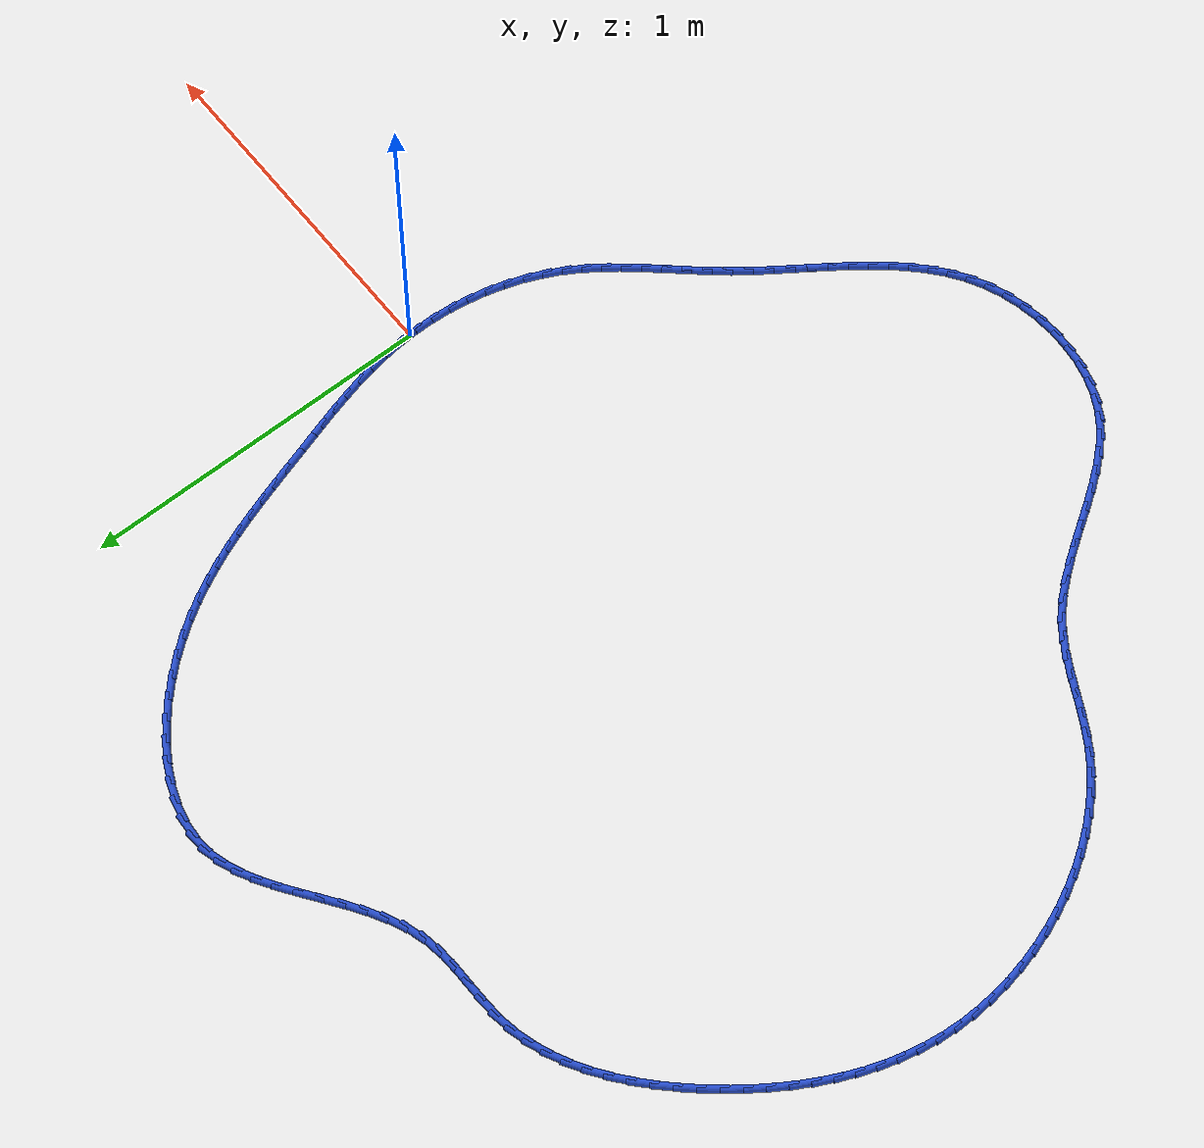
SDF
<sdf version="1.6">
 <world name="default">
  <light name="sun" type="directional">
   <pose>0 0 10 0 -0 0</pose>
   <diffuse>0.8 0.8 0.8 1</diffuse>
   <specular>0.2 0.2 0.2 1</specular>
   <attenuation>
    <range>1000</range>
    <constant>0.9</constant>
    <linear>0.01</linear>
    <quadratic>0.001</quadratic>
   </attenuation>
   <direction>-0.5 0.1 -0.9</direction>
  </light>
  <model name="ground_plane">
   <static>1</static>
   <link name="link">
    <collision name="collision">
     <geometry><plane><normal>0 0 1</normal><size>100 100</size></plane></geometry>
     <surface><friction><ode><mu>100</mu><mu2>50</mu2></ode></friction></surface>
    </collision>
    <visual name="visual">
     <cast_shadows>0</cast_shadows>
     <geometry><plane><normal>0 0 1</normal><size>100 100</size></plane></geometry>
     <material>
      <script><uri>file://media/materials/scripts/gazebo.material</uri><name>Gazebo/WhiteGlow</name></script>
     </material>
    </visual>
   </link>
  </model>
  <gravity>0 0 -9.8</gravity>
  <magnetic_field>6e-06 2.3e-05 -4.2e-05</magnetic_field>
  <atmosphere type="adiabatic"/>
  <physics name="default_physics" default="0" type="ode">
   <max_step_size>0.001</max_step_size>
   <real_time_factor>1</real_time_factor>
   <real_time_update_rate>1000</real_time_update_rate>
  </physics>
  <scene><ambient>0.4 0.4 0.4 1</ambient><background>0.7 0.7 0.7 1</background><shadows>1</shadows></scene>
  <spherical_coordinates>
   <surface_model>EARTH_WGS84</surface_model>
   <latitude_deg>0</latitude_deg>
   <longitude_deg>0</longitude_deg>
   <elevation>0</elevation>
   <heading_deg>0</heading_deg>
  </spherical_coordinates>
  <model name="line">
   <link name="link_0">
    <pose>2.7755575615628914e-17 6.938893903907228e-17 0.01 0 1.57 -1.4930343946396438</pose>
    <collision name="collision">
     <geometry><cylinder><radius>0.01</radius><length>0.08</length></cylinder></geometry>
    </collision>
    <visual name="visual">
     <material>
      <script><name>Gazebo/Blue</name><uri>file://media/materials/scripts/gazebo.material</uri></script>
     </material>
     <geometry><cylinder><radius>0.01</radius><length>0.08</length></cylinder></geometry>
    </visual>
   </link>
   <link name="link_1">
    <pose>-0.004160817956381184 0.053399237261319905 0.01 0 1.57 -1.4353308980526718</pose>
    <collision name="collision">
     <geometry><cylinder><radius>0.01</radius><length>0.08</length></cylinder></geometry>
    </collision>
    <visual name="visual">
     <material>
      <script><name>Gazebo/Blue</name><uri>file://media/materials/scripts/gazebo.material</uri></script>
     </material>
     <geometry><cylinder><radius>0.01</radius><length>0.08</length></cylinder></geometry>
    </visual>
   </link>
   <link name="link_2">
    <pose>-0.011367591553501054 0.10627350995342039 0.01 0 1.57 -1.385889443154771</pose>
    <collision name="collision">
     <geometry><cylinder><radius>0.01</radius><length>0.08</length></cylinder></geometry>
    </collision>
    <visual name="visual">
     <material>
      <script><name>Gazebo/Blue</name><uri>file://media/materials/scripts/gazebo.material</uri></script>
     </material>
     <geometry><cylinder><radius>0.01</radius><length>0.08</length></cylinder></geometry>
    </visual>
   </link>
   <link name="link_3">
    <pose>-0.021170964088978235 0.15868577962882582 0.01 0 1.57 -1.3449548798643165</pose>
    <collision name="collision">
     <geometry><cylinder><radius>0.01</radius><length>0.08</length></cylinder></geometry>
    </collision>
    <visual name="visual">
     <material>
      <script><name>Gazebo/Blue</name><uri>file://media/materials/scripts/gazebo.material</uri></script>
     </material>
     <geometry><cylinder><radius>0.01</radius><length>0.08</length></cylinder></geometry>
    </visual>
   </link>
   <link name="link_4">
    <pose>-0.03312157886043138 0.21069900784006054 0.01 0 1.57 -1.3125814998945433</pose>
    <collision name="collision">
     <geometry><cylinder><radius>0.01</radius><length>0.08</length></cylinder></geometry>
    </collision>
    <visual name="visual">
     <material>
      <script><name>Gazebo/Blue</name><uri>file://media/materials/scripts/gazebo.material</uri></script>
     </material>
     <geometry><cylinder><radius>0.01</radius><length>0.08</length></cylinder></geometry>
    </visual>
   </link>
   <link name="link_5">
    <pose>-0.046770079165479116 0.2623761561396489 0.01 0 1.57 -1.2887208643949528</pose>
    <collision name="collision">
     <geometry><cylinder><radius>0.01</radius><length>0.08</length></cylinder></geometry>
    </collision>
    <visual name="visual">
     <material>
      <script><name>Gazebo/Blue</name><uri>file://media/materials/scripts/gazebo.material</uri></script>
     </material>
     <geometry><cylinder><radius>0.01</radius><length>0.08</length></cylinder></geometry>
    </visual>
   </link>
   <link name="link_6">
    <pose>-0.06166710830174012 0.31378018608011515 0.01 0 1.57 -1.2732926865974128</pose>
    <collision name="collision">
     <geometry><cylinder><radius>0.01</radius><length>0.08</length></cylinder></geometry>
    </collision>
    <visual name="visual">
     <material>
      <script><name>Gazebo/Blue</name><uri>file://media/materials/scripts/gazebo.material</uri></script>
     </material>
     <geometry><cylinder><radius>0.01</radius><length>0.08</length></cylinder></geometry>
    </visual>
   </link>
   <link name="link_7">
    <pose>-0.07736330956683299 0.3649740592139835 0.01 0 1.57 -1.2662359679921242</pose>
    <collision name="collision">
     <geometry><cylinder><radius>0.01</radius><length>0.08</length></cylinder></geometry>
    </collision>
    <visual name="visual">
     <material>
      <script><name>Gazebo/Blue</name><uri>file://media/materials/scripts/gazebo.material</uri></script>
     </material>
     <geometry><cylinder><radius>0.01</radius><length>0.08</length></cylinder></geometry>
    </visual>
   </link>
   <link name="link_8">
    <pose>-0.09340932625837645 0.4160207370937785 0.01 0 1.57 -1.2668757301567348</pose>
    <collision name="collision">
     <geometry><cylinder><radius>0.01</radius><length>0.08</length></cylinder></geometry>
    </collision>
    <visual name="visual">
     <material>
      <script><name>Gazebo/Blue</name><uri>file://media/materials/scripts/gazebo.material</uri></script>
     </material>
     <geometry><cylinder><radius>0.01</radius><length>0.08</length></cylinder></geometry>
    </visual>
   </link>
   <link name="link_9">
    <pose>-0.10939085695951056 0.4669761995077882 0.01 0 1.57 -1.2669979854348807</pose>
    <collision name="collision">
     <geometry><cylinder><radius>0.01</radius><length>0.08</length></cylinder></geometry>
    </collision>
    <visual name="visual">
     <material>
      <script><name>Gazebo/Blue</name><uri>file://media/materials/scripts/gazebo.material</uri></script>
     </material>
     <geometry><cylinder><radius>0.01</radius><length>0.08</length></cylinder></geometry>
    </visual>
   </link>
   <link name="link_10">
    <pose>-0.12532741243108794 0.5178100263105241 0.01 0 1.57 -1.2610130432937554</pose>
    <collision name="collision">
     <geometry><cylinder><radius>0.01</radius><length>0.08</length></cylinder></geometry>
    </collision>
    <visual name="visual">
     <material>
      <script><name>Gazebo/Blue</name><uri>file://media/materials/scripts/gazebo.material</uri></script>
     </material>
     <geometry><cylinder><radius>0.01</radius><length>0.08</length></cylinder></geometry>
    </visual>
   </link>
   <link name="link_11">
    <pose>-0.14153139597585496 0.5684334635947373 0.01 0 1.57 -1.24877902378824</pose>
    <collision name="collision">
     <geometry><cylinder><radius>0.01</radius><length>0.08</length></cylinder></geometry>
    </collision>
    <visual name="visual">
     <material>
      <script><name>Gazebo/Blue</name><uri>file://media/materials/scripts/gazebo.material</uri></script>
     </material>
     <geometry><cylinder><radius>0.01</radius><length>0.08</length></cylinder></geometry>
    </visual>
   </link>
   <link name="link_12">
    <pose>-0.1583207118810469 0.6187566618530104 0.01 0 1.57 -1.2302736473218485</pose>
    <collision name="collision">
     <geometry><cylinder><radius>0.01</radius><length>0.08</length></cylinder></geometry>
    </collision>
    <visual name="visual">
     <material>
      <script><name>Gazebo/Blue</name><uri>file://media/materials/scripts/gazebo.material</uri></script>
     </material>
     <geometry><cylinder><radius>0.01</radius><length>0.08</length></cylinder></geometry>
    </visual>
   </link>
   <link name="link_13">
    <pose>-0.17601326443389884 0.6686897715779242 0.01 0 1.57 -1.2055044147180527</pose>
    <collision name="collision">
     <geometry><cylinder><radius>0.01</radius><length>0.08</length></cylinder></geometry>
    </collision>
    <visual name="visual">
     <material>
      <script><name>Gazebo/Blue</name><uri>file://media/materials/scripts/gazebo.material</uri></script>
     </material>
     <geometry><cylinder><radius>0.01</radius><length>0.08</length></cylinder></geometry>
    </visual>
   </link>
   <link name="link_14">
    <pose>-0.19492695792164585 0.7181429432620606 0.01 0 1.57 -1.1745303983446318</pose>
    <collision name="collision">
     <geometry><cylinder><radius>0.01</radius><length>0.08</length></cylinder></geometry>
    </collision>
    <visual name="visual">
     <material>
      <script><name>Gazebo/Blue</name><uri>file://media/materials/scripts/gazebo.material</uri></script>
     </material>
     <geometry><cylinder><radius>0.01</radius><length>0.08</length></cylinder></geometry>
    </visual>
   </link>
   <link name="link_15">
    <pose>-0.21537969663152312 0.767026327398002 0.01 0 1.57 -1.137490162720606</pose>
    <collision name="collision">
     <geometry><cylinder><radius>0.01</radius><length>0.08</length></cylinder></geometry>
    </collision>
    <visual name="visual">
     <material>
      <script><name>Gazebo/Blue</name><uri>file://media/materials/scripts/gazebo.material</uri></script>
     </material>
     <geometry><cylinder><radius>0.01</radius><length>0.08</length></cylinder></geometry>
    </visual>
   </link>
   <link name="link_16">
    <pose>-0.23768938485076574 0.8152500744783295 0.01 0 1.57 -1.0946333771606531</pose>
    <collision name="collision">
     <geometry><cylinder><radius>0.01</radius><length>0.08</length></cylinder></geometry>
    </collision>
    <visual name="visual">
     <material>
      <script><name>Gazebo/Blue</name><uri>file://media/materials/scripts/gazebo.material</uri></script>
     </material>
     <geometry><cylinder><radius>0.01</radius><length>0.08</length></cylinder></geometry>
    </visual>
   </link>
   <link name="link_17">
    <pose>-0.2621739268666088 0.8627243349956248 0.01 0 1.57 -1.0463518082171472</pose>
    <collision name="collision">
     <geometry><cylinder><radius>0.01</radius><length>0.08</length></cylinder></geometry>
    </collision>
    <visual name="visual">
     <material>
      <script><name>Gazebo/Blue</name><uri>file://media/materials/scripts/gazebo.material</uri></script>
     </material>
     <geometry><cylinder><radius>0.01</radius><length>0.08</length></cylinder></geometry>
    </visual>
   </link>
   <link name="link_18">
    <pose>-0.2891512269662875 0.90935925944247 0.01 0 1.57 -0.9932034220748558</pose>
    <collision name="collision">
     <geometry><cylinder><radius>0.01</radius><length>0.08</length></cylinder></geometry>
    </collision>
    <visual name="visual">
     <material>
      <script><name>Gazebo/Blue</name><uri>file://media/materials/scripts/gazebo.material</uri></script>
     </material>
     <geometry><cylinder><radius>0.01</radius><length>0.08</length></cylinder></geometry>
    </visual>
   </link>
   <link name="link_19">
    <pose>-0.3189391894370368 0.9550649983114464 0.01 0 1.57 -0.9359221242352174</pose>
    <collision name="collision">
     <geometry><cylinder><radius>0.01</radius><length>0.08</length></cylinder></geometry>
    </collision>
    <visual name="visual">
     <material>
      <script><name>Gazebo/Blue</name><uri>file://media/materials/scripts/gazebo.material</uri></script>
     </material>
     <geometry><cylinder><radius>0.01</radius><length>0.08</length></cylinder></geometry>
    </visual>
   </link>
   <link name="link_20">
    <pose>-0.3518557185660921 0.9997517020951361 0.01 0 1.57 -0.875412341350439</pose>
    <collision name="collision">
     <geometry><cylinder><radius>0.01</radius><length>0.08</length></cylinder></geometry>
    </collision>
    <visual name="visual">
     <material>
      <script><name>Gazebo/Blue</name><uri>file://media/materials/scripts/gazebo.material</uri></script>
     </material>
     <geometry><cylinder><radius>0.01</radius><length>0.08</length></cylinder></geometry>
    </visual>
   </link>
   <link name="link_21">
    <pose>-0.388217201862858 1.0433282377707875 0.01 0 1.57 -0.813309775742465</pose>
    <collision name="collision">
     <geometry><cylinder><radius>0.01</radius><length>0.08</length></cylinder></geometry>
    </collision>
    <visual name="visual">
     <material>
      <script><name>Gazebo/Blue</name><uri>file://media/materials/scripts/gazebo.material</uri></script>
     </material>
     <geometry><cylinder><radius>0.01</radius><length>0.08</length></cylinder></geometry>
    </visual>
   </link>
   <link name="link_22">
    <pose>-0.4280924163235601 1.0854939413717943 0.01 0 1.57 -0.7501688002993213</pose>
    <collision name="collision">
     <geometry><cylinder><radius>0.01</radius><length>0.08</length></cylinder></geometry>
    </collision>
    <visual name="visual">
     <material>
      <script><name>Gazebo/Blue</name><uri>file://media/materials/scripts/gazebo.material</uri></script>
     </material>
     <geometry><cylinder><radius>0.01</radius><length>0.08</length></cylinder></geometry>
    </visual>
   </link>
   <link name="link_23">
    <pose>-0.4710302175969798 1.125508185340099 0.01 0 1.57 -0.6837872588697509</pose>
    <collision name="collision">
     <geometry><cylinder><radius>0.01</radius><length>0.08</length></cylinder></geometry>
    </collision>
    <visual name="visual">
     <material>
      <script><name>Gazebo/Blue</name><uri>file://media/materials/scripts/gazebo.material</uri></script>
     </material>
     <geometry><cylinder><radius>0.01</radius><length>0.08</length></cylinder></geometry>
    </visual>
   </link>
   <link name="link_24">
    <pose>-0.5165138928988456 1.1625748573343517 0.01 0 1.57 -0.6116294517948745</pose>
    <collision name="collision">
     <geometry><cylinder><radius>0.01</radius><length>0.08</length></cylinder></geometry>
    </collision>
    <visual name="visual">
     <material>
      <script><name>Gazebo/Blue</name><uri>file://media/materials/scripts/gazebo.material</uri></script>
     </material>
     <geometry><cylinder><radius>0.01</radius><length>0.08</length></cylinder></geometry>
    </visual>
   </link>
   <link name="link_25">
    <pose>-0.5640267294448864 1.1958978450132027 0.01 0 1.57 -0.530886972387727</pose>
    <collision name="collision">
     <geometry><cylinder><radius>0.01</radius><length>0.08</length></cylinder></geometry>
    </collision>
    <visual name="visual">
     <material>
      <script><name>Gazebo/Blue</name><uri>file://media/materials/scripts/gazebo.material</uri></script>
     </material>
     <geometry><cylinder><radius>0.01</radius><length>0.08</length></cylinder></geometry>
    </visual>
   </link>
   <link name="link_26">
    <pose>-0.6130520144508307 1.2246810360353022 0.01 0 1.57 -0.4383353892592471</pose>
    <collision name="collision">
     <geometry><cylinder><radius>0.01</radius><length>0.08</length></cylinder></geometry>
    </collision>
    <visual name="visual">
     <material>
      <script><name>Gazebo/Blue</name><uri>file://media/materials/scripts/gazebo.material</uri></script>
     </material>
     <geometry><cylinder><radius>0.01</radius><length>0.08</length></cylinder></geometry>
    </visual>
   </link>
   <link name="link_27">
    <pose>-0.6630730351324066 1.2481283180592995 0.01 0 1.57 -0.3303143655845333</pose>
    <collision name="collision">
     <geometry><cylinder><radius>0.01</radius><length>0.08</length></cylinder></geometry>
    </collision>
    <visual name="visual">
     <material>
      <script><name>Gazebo/Blue</name><uri>file://media/materials/scripts/gazebo.material</uri></script>
     </material>
     <geometry><cylinder><radius>0.01</radius><length>0.08</length></cylinder></geometry>
    </visual>
   </link>
   <link name="link_28">
    <pose>-0.7135730787053429 1.2654435787438447 0.01 0 1.57 -0.2030037520373873</pose>
    <collision name="collision">
     <geometry><cylinder><radius>0.01</radius><length>0.08</length></cylinder></geometry>
    </collision>
    <visual name="visual">
     <material>
      <script><name>Gazebo/Blue</name><uri>file://media/materials/scripts/gazebo.material</uri></script>
     </material>
     <geometry><cylinder><radius>0.01</radius><length>0.08</length></cylinder></geometry>
    </visual>
   </link>
   <link name="link_29">
    <pose>-0.7640354323853686 1.275830705747589 0.01 0 1.57 -0.05330530101858122</pose>
    <collision name="collision">
     <geometry><cylinder><radius>0.01</radius><length>0.08</length></cylinder></geometry>
    </collision>
    <visual name="visual">
     <material>
      <script><name>Gazebo/Blue</name><uri>file://media/materials/scripts/gazebo.material</uri></script>
     </material>
     <geometry><cylinder><radius>0.01</radius><length>0.08</length></cylinder></geometry>
    </visual>
   </link>
   <link name="link_30">
    <pose>-0.8139433833882117 1.2784935867291811 0.01 0 1.57 0.11872627613931784</pose>
    <collision name="collision">
     <geometry><cylinder><radius>0.01</radius><length>0.08</length></cylinder></geometry>
    </collision>
    <visual name="visual">
     <material>
      <script><name>Gazebo/Blue</name><uri>file://media/materials/scripts/gazebo.material</uri></script>
     </material>
     <geometry><cylinder><radius>0.01</radius><length>0.08</length></cylinder></geometry>
    </visual>
   </link>
   <link name="link_31">
    <pose>-0.8627908148092057 1.2726667089167685 0.01 0 1.57 0.28742687680540807</pose>
    <collision name="collision">
     <geometry><cylinder><radius>0.01</radius><length>0.08</length></cylinder></geometry>
    </collision>
    <visual name="visual">
     <material>
      <script><name>Gazebo/Blue</name><uri>file://media/materials/scripts/gazebo.material</uri></script>
     </material>
     <geometry><cylinder><radius>0.01</radius><length>0.08</length></cylinder></geometry>
    </visual>
   </link>
   <link name="link_32">
    <pose>-0.9104188225058957 1.2585872663871496 0.01 0 1.57 0.4209128819540624</pose>
    <collision name="collision">
     <geometry><cylinder><radius>0.01</radius><length>0.08</length></cylinder></geometry>
    </collision>
    <visual name="visual">
     <material>
      <script><name>Gazebo/Blue</name><uri>file://media/materials/scripts/gazebo.material</uri></script>
     </material>
     <geometry><cylinder><radius>0.01</radius><length>0.08</length></cylinder></geometry>
    </visual>
   </link>
   <link name="link_33">
    <pose>-0.9570853205533928 1.2376961718786608 0.01 0 1.57 0.5177024258035418</pose>
    <collision name="collision">
     <geometry><cylinder><radius>0.01</radius><length>0.08</length></cylinder></geometry>
    </collision>
    <visual name="visual">
     <material>
      <script><name>Gazebo/Blue</name><uri>file://media/materials/scripts/gazebo.material</uri></script>
     </material>
     <geometry><cylinder><radius>0.01</radius><length>0.08</length></cylinder></geometry>
    </visual>
   </link>
   <link name="link_34">
    <pose>-1.0030728858449283 1.2115055612508108 0.01 0 1.57 0.5816566882809583</pose>
    <collision name="collision">
     <geometry><cylinder><radius>0.01</radius><length>0.08</length></cylinder></geometry>
    </collision>
    <visual name="visual">
     <material>
      <script><name>Gazebo/Blue</name><uri>file://media/materials/scripts/gazebo.material</uri></script>
     </material>
     <geometry><cylinder><radius>0.01</radius><length>0.08</length></cylinder></geometry>
    </visual>
   </link>
   <link name="link_35">
    <pose>-1.0486640952737338 1.1815275703631092 0.01 0 1.57 0.6168831982159091</pose>
    <collision name="collision">
     <geometry><cylinder><radius>0.01</radius><length>0.08</length></cylinder></geometry>
    </collision>
    <visual name="visual">
     <material>
      <script><name>Gazebo/Blue</name><uri>file://media/materials/scripts/gazebo.material</uri></script>
     </material>
     <geometry><cylinder><radius>0.01</radius><length>0.08</length></cylinder></geometry>
    </visual>
   </link>
   <link name="link_36">
    <pose>-1.09414152573304 1.1492743350750647 0.01 0 1.57 0.62619913358248</pose>
    <collision name="collision">
     <geometry><cylinder><radius>0.01</radius><length>0.08</length></cylinder></geometry>
    </collision>
    <visual name="visual">
     <material>
      <script><name>Gazebo/Blue</name><uri>file://media/materials/scripts/gazebo.material</uri></script>
     </material>
     <geometry><cylinder><radius>0.01</radius><length>0.08</length></cylinder></geometry>
    </visual>
   </link>
   <link name="link_37">
    <pose>-1.139787754116079 1.1162579912461852 0.01 0 1.57 0.6107113216895229</pose>
    <collision name="collision">
     <geometry><cylinder><radius>0.01</radius><length>0.08</length></cylinder></geometry>
    </collision>
    <visual name="visual">
     <material>
      <script><name>Gazebo/Blue</name><uri>file://media/materials/scripts/gazebo.material</uri></script>
     </material>
     <geometry><cylinder><radius>0.01</radius><length>0.08</length></cylinder></geometry>
    </visual>
   </link>
   <link name="link_38">
    <pose>-1.1858853573160812 1.0839906747359813 0.01 0 1.57 0.5698274325326032</pose>
    <collision name="collision">
     <geometry><cylinder><radius>0.01</radius><length>0.08</length></cylinder></geometry>
    </collision>
    <visual name="visual">
     <material>
      <script><name>Gazebo/Blue</name><uri>file://media/materials/scripts/gazebo.material</uri></script>
     </material>
     <geometry><cylinder><radius>0.01</radius><length>0.08</length></cylinder></geometry>
    </visual>
   </link>
   <link name="link_39">
    <pose>-1.2327169122262789 1.0539845214039603 0.01 0 1.57 0.5015009381086317</pose>
    <collision name="collision">
     <geometry><cylinder><radius>0.01</radius><length>0.08</length></cylinder></geometry>
    </collision>
    <visual name="visual">
     <material>
      <script><name>Gazebo/Blue</name><uri>file://media/materials/scripts/gazebo.material</uri></script>
     </material>
     <geometry><cylinder><radius>0.01</radius><length>0.08</length></cylinder></geometry>
    </visual>
   </link>
   <link name="link_40">
    <pose>-1.2805649957399017 1.027751667109632 0.01 0 1.57 0.4029018999677981</pose>
    <collision name="collision">
     <geometry><cylinder><radius>0.01</radius><length>0.08</length></cylinder></geometry>
    </collision>
    <visual name="visual">
     <material>
      <script><name>Gazebo/Blue</name><uri>file://media/materials/scripts/gazebo.material</uri></script>
     </material>
     <geometry><cylinder><radius>0.01</radius><length>0.08</length></cylinder></geometry>
    </visual>
   </link>
   <link name="link_41">
    <pose>-1.3297121847501825 1.006804247712505 0.01 0 1.57 0.2721472239329551</pose>
    <collision name="collision">
     <geometry><cylinder><radius>0.01</radius><length>0.08</length></cylinder></geometry>
    </collision>
    <visual name="visual">
     <material>
      <script><name>Gazebo/Blue</name><uri>file://media/materials/scripts/gazebo.material</uri></script>
     </material>
     <geometry><cylinder><radius>0.01</radius><length>0.08</length></cylinder></geometry>
    </visual>
   </link>
   <link name="link_42">
    <pose>-1.3804396374061165 0.9926476763889887 0.01 0 1.57 0.1345304223217582</pose>
    <collision name="collision">
     <geometry><cylinder><radius>0.01</radius><length>0.08</length></cylinder></geometry>
    </collision>
    <visual name="visual">
     <material>
      <script><name>Gazebo/Blue</name><uri>file://media/materials/scripts/gazebo.material</uri></script>
     </material>
     <geometry><cylinder><radius>0.01</radius><length>0.08</length></cylinder></geometry>
    </visual>
   </link>
   <link name="link_43">
    <pose>-1.4327705037528438 0.9855648015450075 0.01 0 1.57 0.04417707886031743</pose>
    <collision name="collision">
     <geometry><cylinder><radius>0.01</radius><length>0.08</length></cylinder></geometry>
    </collision>
    <visual name="visual">
     <material>
      <script><name>Gazebo/Blue</name><uri>file://media/materials/scripts/gazebo.material</uri></script>
     </material>
     <geometry><cylinder><radius>0.01</radius><length>0.08</length></cylinder></geometry>
    </visual>
   </link>
   <link name="link_44">
    <pose>-1.4861719895757746 0.9832041439970333 0.01 0 1.57 0.006169271556818146</pose>
    <collision name="collision">
     <geometry><cylinder><radius>0.01</radius><length>0.08</length></cylinder></geometry>
    </collision>
    <visual name="visual">
     <material>
      <script><name>Gazebo/Blue</name><uri>file://media/materials/scripts/gazebo.material</uri></script>
     </material>
     <geometry><cylinder><radius>0.01</radius><length>0.08</length></cylinder></geometry>
    </visual>
   </link>
   <link name="link_45">
    <pose>-1.5400390400083295 0.9828718193188567 0.01 0 1.57 0.018570758008508312</pose>
    <collision name="collision">
     <geometry><cylinder><radius>0.01</radius><length>0.08</length></cylinder></geometry>
    </collision>
    <visual name="visual">
     <material>
      <script><name>Gazebo/Blue</name><uri>file://media/materials/scripts/gazebo.material</uri></script>
     </material>
     <geometry><cylinder><radius>0.01</radius><length>0.08</length></cylinder></geometry>
    </visual>
   </link>
   <link name="link_46">
    <pose>-1.5937666001839301 0.9818739430842693 0.01 0 1.57 0.08205473744704245</pose>
    <collision name="collision">
     <geometry><cylinder><radius>0.01</radius><length>0.08</length></cylinder></geometry>
    </collision>
    <visual name="visual">
     <material>
      <script><name>Gazebo/Blue</name><uri>file://media/materials/scripts/gazebo.material</uri></script>
     </material>
     <geometry><cylinder><radius>0.01</radius><length>0.08</length></cylinder></geometry>
    </visual>
   </link>
   <link name="link_47">
    <pose>-1.6467496188432393 0.9775166518217903 0.01 0 1.57 0.18775828966132785</pose>
    <collision name="collision">
     <geometry><cylinder><radius>0.01</radius><length>0.08</length></cylinder></geometry>
    </collision>
    <visual name="visual">
     <material>
      <script><name>Gazebo/Blue</name><uri>file://media/materials/scripts/gazebo.material</uri></script>
     </material>
     <geometry><cylinder><radius>0.01</radius><length>0.08</length></cylinder></geometry>
    </visual>
   </link>
   <link name="link_48">
    <pose>-1.698483129375822 0.9676874808317317 0.01 0 1.57 0.29531635747888274</pose>
    <collision name="collision">
     <geometry><cylinder><radius>0.01</radius><length>0.08</length></cylinder></geometry>
    </collision>
    <visual name="visual">
     <material>
      <script><name>Gazebo/Blue</name><uri>file://media/materials/scripts/gazebo.material</uri></script>
     </material>
     <geometry><cylinder><radius>0.01</radius><length>0.08</length></cylinder></geometry>
    </visual>
   </link>
   <link name="link_49">
    <pose>-1.7488235589084793 0.9523733270774972 0.01 0 1.57 0.3942623339631377</pose>
    <collision name="collision">
     <geometry><cylinder><radius>0.01</radius><length>0.08</length></cylinder></geometry>
    </collision>
    <visual name="visual">
     <material>
      <script><name>Gazebo/Blue</name><uri>file://media/materials/scripts/gazebo.material</uri></script>
     </material>
     <geometry><cylinder><radius>0.01</radius><length>0.08</length></cylinder></geometry>
    </visual>
   </link>
   <link name="link_50">
    <pose>-1.7977088773679162 0.9320347753880392 0.01 0 1.57 0.48401071138145113</pose>
    <collision name="collision">
     <geometry><cylinder><radius>0.01</radius><length>0.08</length></cylinder></geometry>
    </collision>
    <visual name="visual">
     <material>
      <script><name>Gazebo/Blue</name><uri>file://media/materials/scripts/gazebo.material</uri></script>
     </material>
     <geometry><cylinder><radius>0.01</radius><length>0.08</length></cylinder></geometry>
    </visual>
   </link>
   <link name="link_51">
    <pose>-1.8450770546808362 0.9071324105923102 0.01 0 1.57 0.5646611842871024</pose>
    <collision name="collision">
     <geometry><cylinder><radius>0.01</radius><length>0.08</length></cylinder></geometry>
    </collision>
    <visual name="visual">
     <material>
      <script><name>Gazebo/Blue</name><uri>file://media/materials/scripts/gazebo.material</uri></script>
     </material>
     <geometry><cylinder><radius>0.01</radius><length>0.08</length></cylinder></geometry>
    </visual>
   </link>
   <link name="link_52">
    <pose>-1.8908660607739434 0.8781268175192626 0.01 0 1.57 0.6367608606234233</pose>
    <collision name="collision">
     <geometry><cylinder><radius>0.01</radius><length>0.08</length></cylinder></geometry>
    </collision>
    <visual name="visual">
     <material>
      <script><name>Gazebo/Blue</name><uri>file://media/materials/scripts/gazebo.material</uri></script>
     </material>
     <geometry><cylinder><radius>0.01</radius><length>0.08</length></cylinder></geometry>
    </visual>
   </link>
   <link name="link_53">
    <pose>-1.9350138655739417 0.845478580997849 0.01 0 1.57 0.7010977648688959</pose>
    <collision name="collision">
     <geometry><cylinder><radius>0.01</radius><length>0.08</length></cylinder></geometry>
    </collision>
    <visual name="visual">
     <material>
      <script><name>Gazebo/Blue</name><uri>file://media/materials/scripts/gazebo.material</uri></script>
     </material>
     <geometry><cylinder><radius>0.01</radius><length>0.08</length></cylinder></geometry>
    </visual>
   </link>
   <link name="link_54">
    <pose>-1.977458439007535 0.8096482858570216 0.01 0 1.57 0.7585522349600228</pose>
    <collision name="collision">
     <geometry><cylinder><radius>0.01</radius><length>0.08</length></cylinder></geometry>
    </collision>
    <visual name="visual">
     <material>
      <script><name>Gazebo/Blue</name><uri>file://media/materials/scripts/gazebo.material</uri></script>
     </material>
     <geometry><cylinder><radius>0.01</radius><length>0.08</length></cylinder></geometry>
    </visual>
   </link>
   <link name="link_55">
    <pose>-2.0181377510014284 0.7710965169257332 0.01 0 1.57 0.8100043218370406</pose>
    <collision name="collision">
     <geometry><cylinder><radius>0.01</radius><length>0.08</length></cylinder></geometry>
    </collision>
    <visual name="visual">
     <material>
      <script><name>Gazebo/Blue</name><uri>file://media/materials/scripts/gazebo.material</uri></script>
     </material>
     <geometry><cylinder><radius>0.01</radius><length>0.08</length></cylinder></geometry>
    </visual>
   </link>
   <link name="link_56">
    <pose>-2.0569897714823253 0.7302838590329364 0.01 0 1.57 0.856284110767049</pose>
    <collision name="collision">
     <geometry><cylinder><radius>0.01</radius><length>0.08</length></cylinder></geometry>
    </collision>
    <visual name="visual">
     <material>
      <script><name>Gazebo/Blue</name><uri>file://media/materials/scripts/gazebo.material</uri></script>
     </material>
     <geometry><cylinder><radius>0.01</radius><length>0.08</length></cylinder></geometry>
    </visual>
   </link>
   <link name="link_57">
    <pose>-2.093952470376929 0.687670897007583 0.01 0 1.57 0.898159728653412</pose>
    <collision name="collision">
     <geometry><cylinder><radius>0.01</radius><length>0.08</length></cylinder></geometry>
    </collision>
    <visual name="visual">
     <material>
      <script><name>Gazebo/Blue</name><uri>file://media/materials/scripts/gazebo.material</uri></script>
     </material>
     <geometry><cylinder><radius>0.01</radius><length>0.08</length></cylinder></geometry>
    </visual>
   </link>
   <link name="link_58">
    <pose>-2.128963661512001 0.6437176161834735 0.01 0 1.57 0.938141733169309</pose>
    <collision name="collision">
     <geometry><cylinder><radius>0.01</radius><length>0.08</length></cylinder></geometry>
    </collision>
    <visual name="visual">
     <material>
      <script><name>Gazebo/Blue</name><uri>file://media/materials/scripts/gazebo.material</uri></script>
     </material>
     <geometry><cylinder><radius>0.01</radius><length>0.08</length></cylinder></geometry>
    </visual>
   </link>
   <link name="link_59">
    <pose>-2.1619281352241644 0.5987571765944075 0.01 0 1.57 0.9807251590077517</pose>
    <collision name="collision">
     <geometry><cylinder><radius>0.01</radius><length>0.08</length></cylinder></geometry>
    </collision>
    <visual name="visual">
     <material>
      <script><name>Gazebo/Blue</name><uri>file://media/materials/scripts/gazebo.material</uri></script>
     </material>
     <geometry><cylinder><radius>0.01</radius><length>0.08</length></cylinder></geometry>
    </visual>
   </link>
   <link name="link_60">
    <pose>-2.1926770362806183 0.5528399056178768 0.01 0 1.57 1.0266617675713505</pose>
    <collision name="collision">
     <geometry><cylinder><radius>0.01</radius><length>0.08</length></cylinder></geometry>
    </collision>
    <visual name="visual">
     <material>
      <script><name>Gazebo/Blue</name><uri>file://media/materials/scripts/gazebo.material</uri></script>
     </material>
     <geometry><cylinder><radius>0.01</radius><length>0.08</length></cylinder></geometry>
    </visual>
   </link>
   <link name="link_61">
    <pose>-2.2210315500183637 0.5059778818660913 0.01 0 1.57 1.0761139163103117</pose>
    <collision name="collision">
     <geometry><cylinder><radius>0.01</radius><length>0.08</length></cylinder></geometry>
    </collision>
    <visual name="visual">
     <material>
      <script><name>Gazebo/Blue</name><uri>file://media/materials/scripts/gazebo.material</uri></script>
     </material>
     <geometry><cylinder><radius>0.01</radius><length>0.08</length></cylinder></geometry>
    </visual>
   </link>
   <link name="link_62">
    <pose>-2.2468128617744005 0.4581831839512634 0.01 0 1.57 1.1291998154365601</pose>
    <collision name="collision">
     <geometry><cylinder><radius>0.01</radius><length>0.08</length></cylinder></geometry>
    </collision>
    <visual name="visual">
     <material>
      <script><name>Gazebo/Blue</name><uri>file://media/materials/scripts/gazebo.material</uri></script>
     </material>
     <geometry><cylinder><radius>0.01</radius><length>0.08</length></cylinder></geometry>
    </visual>
   </link>
   <link name="link_63">
    <pose>-2.269842156885729 0.4094678904856034 0.01 0 1.57 1.1859728442675448</pose>
    <collision name="collision">
     <geometry><cylinder><radius>0.01</radius><length>0.08</length></cylinder></geometry>
    </collision>
    <visual name="visual">
     <material>
      <script><name>Gazebo/Blue</name><uri>file://media/materials/scripts/gazebo.material</uri></script>
     </material>
     <geometry><cylinder><radius>0.01</radius><length>0.08</length></cylinder></geometry>
    </visual>
   </link>
   <link name="link_64">
    <pose>-2.2899406206893484 0.35984408008132346 0.01 0 1.57 1.2463984577745113</pose>
    <collision name="collision">
     <geometry><cylinder><radius>0.01</radius><length>0.08</length></cylinder></geometry>
    </collision>
    <visual name="visual">
     <material>
      <script><name>Gazebo/Blue</name><uri>file://media/materials/scripts/gazebo.material</uri></script>
     </material>
     <geometry><cylinder><radius>0.01</radius><length>0.08</length></cylinder></geometry>
    </visual>
   </link>
   <link name="link_65">
    <pose>-2.3069294385222596 0.30932383135063446 0.01 0 1.57 1.3103308521346704</pose>
    <collision name="collision">
     <geometry><cylinder><radius>0.01</radius><length>0.08</length></cylinder></geometry>
    </collision>
    <visual name="visual">
     <material>
      <script><name>Gazebo/Blue</name><uri>file://media/materials/scripts/gazebo.material</uri></script>
     </material>
     <geometry><cylinder><radius>0.01</radius><length>0.08</length></cylinder></geometry>
    </visual>
   </link>
   <link name="link_66">
    <pose>-2.320629795721463 0.25791922290574715 0.01 0 1.57 1.3774928217987614</pose>
    <collision name="collision">
     <geometry><cylinder><radius>0.01</radius><length>0.08</length></cylinder></geometry>
    </collision>
    <visual name="visual">
     <material>
      <script><name>Gazebo/Blue</name><uri>file://media/materials/scripts/gazebo.material</uri></script>
     </material>
     <geometry><cylinder><radius>0.01</radius><length>0.08</length></cylinder></geometry>
    </visual>
   </link>
   <link name="link_67">
    <pose>-2.330862877623958 0.2056423333588738 0.01 0 1.57 1.4474632756569723</pose>
    <collision name="collision">
     <geometry><cylinder><radius>0.01</radius><length>0.08</length></cylinder></geometry>
    </collision>
    <visual name="visual">
     <material>
      <script><name>Gazebo/Blue</name><uri>file://media/materials/scripts/gazebo.material</uri></script>
     </material>
     <geometry><cylinder><radius>0.01</radius><length>0.08</length></cylinder></geometry>
    </visual>
   </link>
   <link name="link_68">
    <pose>-2.3374498695667456 0.15250524132222465 0.01 0 1.57 1.519458174033487</pose>
    <collision name="collision">
     <geometry><cylinder><radius>0.01</radius><length>0.08</length></cylinder></geometry>
    </collision>
    <visual name="visual">
     <material>
      <script><name>Gazebo/Blue</name><uri>file://media/materials/scripts/gazebo.material</uri></script>
     </material>
     <geometry><cylinder><radius>0.01</radius><length>0.08</length></cylinder></geometry>
    </visual>
   </link>
   <link name="link_69">
    <pose>-2.3402231965632354 0.09853192998272314 0.01 0 1.57 -1.5515024114023652</pose>
    <collision name="collision">
     <geometry><cylinder><radius>0.01</radius><length>0.08</length></cylinder></geometry>
    </collision>
    <visual name="visual">
     <material>
      <script><name>Gazebo/Blue</name><uri>file://media/materials/scripts/gazebo.material</uri></script>
     </material>
     <geometry><cylinder><radius>0.01</radius><length>0.08</length></cylinder></geometry>
    </visual>
   </link>
   <link name="link_70">
    <pose>-2.3391691830316934 0.04390938606015118 0.01 0 1.57 -1.4839901937349684</pose>
    <collision name="collision">
     <geometry><cylinder><radius>0.01</radius><length>0.08</length></cylinder></geometry>
    </collision>
    <visual name="visual">
     <material>
      <script><name>Gazebo/Blue</name><uri>file://media/materials/scripts/gazebo.material</uri></script>
     </material>
     <geometry><cylinder><radius>0.01</radius><length>0.08</length></cylinder></geometry>
    </visual>
   </link>
   <link name="link_71">
    <pose>-2.334385722236039 -0.011057234873687241 0.01 0 1.57 -1.4190256809080213</pose>
    <collision name="collision">
     <geometry><cylinder><radius>0.01</radius><length>0.08</length></cylinder></geometry>
    </collision>
    <visual name="visual">
     <material>
      <script><name>Gazebo/Blue</name><uri>file://media/materials/scripts/gazebo.material</uri></script>
     </material>
     <geometry><cylinder><radius>0.01</radius><length>0.08</length></cylinder></geometry>
    </visual>
   </link>
   <link name="link_72">
    <pose>-2.325973205463485 -0.06606013144973769 0.01 0 1.57 -1.3559845635253618</pose>
    <collision name="collision">
     <geometry><cylinder><radius>0.01</radius><length>0.08</length></cylinder></geometry>
    </collision>
    <visual name="visual">
     <material>
      <script><name>Gazebo/Blue</name><uri>file://media/materials/scripts/gazebo.material</uri></script>
     </material>
     <geometry><cylinder><radius>0.01</radius><length>0.08</length></cylinder></geometry>
    </visual>
   </link>
   <link name="link_73">
    <pose>-2.314032024001246 -0.12079150229894628 0.01 0 1.57 -1.294248490838585</pose>
    <collision name="collision">
     <geometry><cylinder><radius>0.01</radius><length>0.08</length></cylinder></geometry>
    </collision>
    <visual name="visual">
     <material>
      <script><name>Gazebo/Blue</name><uri>file://media/materials/scripts/gazebo.material</uri></script>
     </material>
     <geometry><cylinder><radius>0.01</radius><length>0.08</length></cylinder></geometry>
    </visual>
   </link>
   <link name="link_74">
    <pose>-2.2986625691365363 -0.17494354605225665 0.01 0 1.57 -1.2332083232858182</pose>
    <collision name="collision">
     <geometry><cylinder><radius>0.01</radius><length>0.08</length></cylinder></geometry>
    </collision>
    <visual name="visual">
     <material>
      <script><name>Gazebo/Blue</name><uri>file://media/materials/scripts/gazebo.material</uri></script>
     </material>
     <geometry><cylinder><radius>0.01</radius><length>0.08</length></cylinder></geometry>
    </visual>
   </link>
   <link name="link_75">
    <pose>-2.2799652321565684 -0.22820846134061482 0.01 0 1.57 -1.1722637116177694</pose>
    <collision name="collision">
     <geometry><cylinder><radius>0.01</radius><length>0.08</length></cylinder></geometry>
    </collision>
    <visual name="visual">
     <material>
      <script><name>Gazebo/Blue</name><uri>file://media/materials/scripts/gazebo.material</uri></script>
     </material>
     <geometry><cylinder><radius>0.01</radius><length>0.08</length></cylinder></geometry>
    </visual>
   </link>
   <link name="link_76">
    <pose>-2.258040404348558 -0.2802784467949662 0.01 0 1.57 -1.1108210417435693</pose>
    <collision name="collision">
     <geometry><cylinder><radius>0.01</radius><length>0.08</length></cylinder></geometry>
    </collision>
    <visual name="visual">
     <material>
      <script><name>Gazebo/Blue</name><uri>file://media/materials/scripts/gazebo.material</uri></script>
     </material>
     <geometry><cylinder><radius>0.01</radius><length>0.08</length></cylinder></geometry>
    </visual>
   </link>
   <link name="link_77">
    <pose>-2.2329884769997173 -0.33084570104625594 0.01 0 1.57 -1.0482914871741256</pose>
    <collision name="collision">
     <geometry><cylinder><radius>0.01</radius><length>0.08</length></cylinder></geometry>
    </collision>
    <visual name="visual">
     <material>
      <script><name>Gazebo/Blue</name><uri>file://media/materials/scripts/gazebo.material</uri></script>
     </material>
     <geometry><cylinder><radius>0.01</radius><length>0.08</length></cylinder></geometry>
    </visual>
   </link>
   <link name="link_78">
    <pose>-2.204909841397261 -0.37960242272543004 0.01 0 1.57 -0.9840908262998647</pose>
    <collision name="collision">
     <geometry><cylinder><radius>0.01</radius><length>0.08</length></cylinder></geometry>
    </collision>
    <visual name="visual">
     <material>
      <script><name>Gazebo/Blue</name><uri>file://media/materials/scripts/gazebo.material</uri></script>
     </material>
     <geometry><cylinder><radius>0.01</radius><length>0.08</length></cylinder></geometry>
    </visual>
   </link>
   <link name="link_79">
    <pose>-2.1739048888284036 -0.42624081046343243 0.01 0 1.57 -0.9176427914935024</pose>
    <collision name="collision">
     <geometry><cylinder><radius>0.01</radius><length>0.08</length></cylinder></geometry>
    </collision>
    <visual name="visual">
     <material>
      <script><name>Gazebo/Blue</name><uri>file://media/materials/scripts/gazebo.material</uri></script>
     </material>
     <geometry><cylinder><radius>0.01</radius><length>0.08</length></cylinder></geometry>
    </visual>
   </link>
   <link name="link_80">
    <pose>-2.140074010580358 -0.470453062891209 0.01 0 1.57 -0.8483879618926762</pose>
    <collision name="collision">
     <geometry><cylinder><radius>0.01</radius><length>0.08</length></cylinder></geometry>
    </collision>
    <visual name="visual">
     <material>
      <script><name>Gazebo/Blue</name><uri>file://media/materials/scripts/gazebo.material</uri></script>
     </material>
     <geometry><cylinder><radius>0.01</radius><length>0.08</length></cylinder></geometry>
    </visual>
   </link>
   <link name="link_81">
    <pose>-2.1035175979403387 -0.511931378639705 0.01 0 1.57 -0.7758004684172046</pose>
    <collision name="collision">
     <geometry><cylinder><radius>0.01</radius><length>0.08</length></cylinder></geometry>
    </collision>
    <visual name="visual">
     <material>
      <script><name>Gazebo/Blue</name><uri>file://media/materials/scripts/gazebo.material</uri></script>
     </material>
     <geometry><cylinder><radius>0.01</radius><length>0.08</length></cylinder></geometry>
    </visual>
   </link>
   <link name="link_82">
    <pose>-2.0643360421955594 -0.5503679563398665 0.01 0 1.57 -0.6994148171113642</pose>
    <collision name="collision">
     <geometry><cylinder><radius>0.01</radius><length>0.08</length></cylinder></geometry>
    </collision>
    <visual name="visual">
     <material>
      <script><name>Gazebo/Blue</name><uri>file://media/materials/scripts/gazebo.material</uri></script>
     </material>
     <geometry><cylinder><radius>0.01</radius><length>0.08</length></cylinder></geometry>
    </visual>
   </link>
   <link name="link_83">
    <pose>-2.0226297346332336 -0.5854549946226371 0.01 0 1.57 -0.618901962641189</pose>
    <collision name="collision">
     <geometry><cylinder><radius>0.01</radius><length>0.08</length></cylinder></geometry>
    </collision>
    <visual name="visual">
     <material>
      <script><name>Gazebo/Blue</name><uri>file://media/materials/scripts/gazebo.material</uri></script>
     </material>
     <geometry><cylinder><radius>0.01</radius><length>0.08</length></cylinder></geometry>
    </visual>
   </link>
   <link name="link_84">
    <pose>-1.9784999857387948 -0.6168865245403592 0.01 0 1.57 -0.5434845534858664</pose>
    <collision name="collision">
     <geometry><cylinder><radius>0.01</radius><length>0.08</length></cylinder></geometry>
    </collision>
    <visual name="visual">
     <material>
      <script><name>Gazebo/Blue</name><uri>file://media/materials/scripts/gazebo.material</uri></script>
     </material>
     <geometry><cylinder><radius>0.01</radius><length>0.08</length></cylinder></geometry>
    </visual>
   </link>
   <link name="link_85">
    <pose>-1.9322771822967675 -0.6448132406850418 0.01 0 1.57 -0.4951447742859604</pose>
    <collision name="collision">
     <geometry><cylinder><radius>0.01</radius><length>0.08</length></cylinder></geometry>
    </collision>
    <visual name="visual">
     <material>
      <script><name>Gazebo/Blue</name><uri>file://media/materials/scripts/gazebo.material</uri></script>
     </material>
     <geometry><cylinder><radius>0.01</radius><length>0.08</length></cylinder></geometry>
    </visual>
   </link>
   <link name="link_86">
    <pose>-1.8848207275466864 -0.6704404318072357 0.01 0 1.57 -0.47701226002974445</pose>
    <collision name="collision">
     <geometry><cylinder><radius>0.01</radius><length>0.08</length></cylinder></geometry>
    </collision>
    <visual name="visual">
     <material>
      <script><name>Gazebo/Blue</name><uri>file://media/materials/scripts/gazebo.material</uri></script>
     </material>
     <geometry><cylinder><radius>0.01</radius><length>0.08</length></cylinder></geometry>
    </visual>
   </link>
   <link name="link_87">
    <pose>-1.8370644658792625 -0.6951217850720314 0.01 0 1.57 -0.4892523987174185</pose>
    <collision name="collision">
     <geometry><cylinder><radius>0.01</radius><length>0.08</length></cylinder></geometry>
    </collision>
    <visual name="visual">
     <material>
      <script><name>Gazebo/Blue</name><uri>file://media/materials/scripts/gazebo.material</uri></script>
     </material>
     <geometry><cylinder><radius>0.01</radius><length>0.08</length></cylinder></geometry>
    </visual>
   </link>
   <link name="link_88">
    <pose>-1.7899422416852087 -0.7202109876445183 0.01 0 1.57 -0.5326053720112373</pose>
    <collision name="collision">
     <geometry><cylinder><radius>0.01</radius><length>0.08</length></cylinder></geometry>
    </collision>
    <visual name="visual">
     <material>
      <script><name>Gazebo/Blue</name><uri>file://media/materials/scripts/gazebo.material</uri></script>
     </material>
     <geometry><cylinder><radius>0.01</radius><length>0.08</length></cylinder></geometry>
    </visual>
   </link>
   <link name="link_89">
    <pose>-1.744387899355237 -0.747061726689787 0.01 0 1.57 -0.608057349786397</pose>
    <collision name="collision">
     <geometry><cylinder><radius>0.01</radius><length>0.08</length></cylinder></geometry>
    </collision>
    <visual name="visual">
     <material>
      <script><name>Gazebo/Blue</name><uri>file://media/materials/scripts/gazebo.material</uri></script>
     </material>
     <geometry><cylinder><radius>0.01</radius><length>0.08</length></cylinder></geometry>
    </visual>
   </link>
   <link name="link_90">
    <pose>-1.7013352832800597 -0.7770276893729273 0.01 0 1.57 -0.7126815950881396</pose>
    <collision name="collision">
     <geometry><cylinder><radius>0.01</radius><length>0.08</length></cylinder></geometry>
    </collision>
    <visual name="visual">
     <material>
      <script><name>Gazebo/Blue</name><uri>file://media/materials/scripts/gazebo.material</uri></script>
     </material>
     <geometry><cylinder><radius>0.01</radius><length>0.08</length></cylinder></geometry>
    </visual>
   </link>
   <link name="link_91">
    <pose>-1.6616309877596263 -0.8113402280332115 0.01 0 1.57 -0.813413997352669</pose>
    <collision name="collision">
     <geometry><cylinder><radius>0.01</radius><length>0.08</length></cylinder></geometry>
    </collision>
    <visual name="visual">
     <material>
      <script><name>Gazebo/Blue</name><uri>file://media/materials/scripts/gazebo.material</uri></script>
     </material>
     <geometry><cylinder><radius>0.01</radius><length>0.08</length></cylinder></geometry>
    </visual>
   </link>
   <link name="link_92">
    <pose>-1.625172929646361 -0.8499005383385716 0.01 0 1.57 -0.8905216383640661</pose>
    <collision name="collision">
     <geometry><cylinder><radius>0.01</radius><length>0.08</length></cylinder></geometry>
    </collision>
    <visual name="visual">
     <material>
      <script><name>Gazebo/Blue</name><uri>file://media/materials/scripts/gazebo.material</uri></script>
     </material>
     <geometry><cylinder><radius>0.01</radius><length>0.08</length></cylinder></geometry>
    </visual>
   </link>
   <link name="link_93">
    <pose>-1.591276752775711 -0.891793401125863 0.01 0 1.57 -0.9448092618558369</pose>
    <collision name="collision">
     <geometry><cylinder><radius>0.01</radius><length>0.08</length></cylinder></geometry>
    </collision>
    <visual name="visual">
     <material>
      <script><name>Gazebo/Blue</name><uri>file://media/materials/scripts/gazebo.material</uri></script>
     </material>
     <geometry><cylinder><radius>0.01</radius><length>0.08</length></cylinder></geometry>
    </visual>
   </link>
   <link name="link_94">
    <pose>-1.559249650614877 -0.9360917488279049 0.01 0 1.57 -0.9777746125072948</pose>
    <collision name="collision">
     <geometry><cylinder><radius>0.01</radius><length>0.08</length></cylinder></geometry>
    </collision>
    <visual name="visual">
     <material>
      <script><name>Gazebo/Blue</name><uri>file://media/materials/scripts/gazebo.material</uri></script>
     </material>
     <geometry><cylinder><radius>0.01</radius><length>0.08</length></cylinder></geometry>
    </visual>
   </link>
   <link name="link_95">
    <pose>-1.5283988166310603 -0.981868513877517 0.01 0 1.57 -0.9905750589263191</pose>
    <collision name="collision">
     <geometry><cylinder><radius>0.01</radius><length>0.08</length></cylinder></geometry>
    </collision>
    <visual name="visual">
     <material>
      <script><name>Gazebo/Blue</name><uri>file://media/materials/scripts/gazebo.material</uri></script>
     </material>
     <geometry><cylinder><radius>0.01</radius><length>0.08</length></cylinder></geometry>
    </visual>
   </link>
   <link name="link_96">
    <pose>-1.4980314442914622 -1.0281966287075168 0.01 0 1.57 -0.9836712761746488</pose>
    <collision name="collision">
     <geometry><cylinder><radius>0.01</radius><length>0.08</length></cylinder></geometry>
    </collision>
    <visual name="visual">
     <material>
      <script><name>Gazebo/Blue</name><uri>file://media/materials/scripts/gazebo.material</uri></script>
     </material>
     <geometry><cylinder><radius>0.01</radius><length>0.08</length></cylinder></geometry>
    </visual>
   </link>
   <link name="link_97">
    <pose>-1.467454727063284 -1.0741490257507247 0.01 0 1.57 -0.9567091832966185</pose>
    <collision name="collision">
     <geometry><cylinder><radius>0.01</radius><length>0.08</length></cylinder></geometry>
    </collision>
    <visual name="visual">
     <material>
      <script><name>Gazebo/Blue</name><uri>file://media/materials/scripts/gazebo.material</uri></script>
     </material>
     <geometry><cylinder><radius>0.01</radius><length>0.08</length></cylinder></geometry>
    </visual>
   </link>
   <link name="link_98">
    <pose>-1.4359758584137265 -1.118798637439959 0.01 0 1.57 -0.9085691793149548</pose>
    <collision name="collision">
     <geometry><cylinder><radius>0.01</radius><length>0.08</length></cylinder></geometry>
    </collision>
    <visual name="visual">
     <material>
      <script><name>Gazebo/Blue</name><uri>file://media/materials/scripts/gazebo.material</uri></script>
     </material>
     <geometry><cylinder><radius>0.01</radius><length>0.08</length></cylinder></geometry>
    </visual>
   </link>
   <link name="link_99">
    <pose>-1.4029020318099907 -1.1612183962080396 0.01 0 1.57 -0.8376290341643458</pose>
    <collision name="collision">
     <geometry><cylinder><radius>0.01</radius><length>0.08</length></cylinder></geometry>
    </collision>
    <visual name="visual">
     <material>
      <script><name>Gazebo/Blue</name><uri>file://media/materials/scripts/gazebo.material</uri></script>
     </material>
     <geometry><cylinder><radius>0.01</radius><length>0.08</length></cylinder></geometry>
    </visual>
   </link>
   <link name="link_100">
    <pose>-1.3675404407192784 -1.2004812344877864 0.01 0 1.57 -0.7423987276970806</pose>
    <collision name="collision">
     <geometry><cylinder><radius>0.01</radius><length>0.08</length></cylinder></geometry>
    </collision>
    <visual name="visual">
     <material>
      <script><name>Gazebo/Blue</name><uri>file://media/materials/scripts/gazebo.material</uri></script>
     </material>
     <geometry><cylinder><radius>0.01</radius><length>0.08</length></cylinder></geometry>
    </visual>
   </link>
   <link name="link_101">
    <pose>-1.3291982786087906 -1.2356600847120165 0.01 0 1.57 -0.6227146331196723</pose>
    <collision name="collision">
     <geometry><cylinder><radius>0.01</radius><length>0.08</length></cylinder></geometry>
    </collision>
    <visual name="visual">
     <material>
      <script><name>Gazebo/Blue</name><uri>file://media/materials/scripts/gazebo.material</uri></script>
     </material>
     <geometry><cylinder><radius>0.01</radius><length>0.08</length></cylinder></geometry>
    </visual>
   </link>
   <link name="link_102">
    <pose>-1.2871827389457282 -1.2658278793135502 0.01 0 1.57 -0.4826111273359344</pose>
    <collision name="collision">
     <geometry><cylinder><radius>0.01</radius><length>0.08</length></cylinder></geometry>
    </collision>
    <visual name="visual">
     <material>
      <script><name>Gazebo/Blue</name><uri>file://media/materials/scripts/gazebo.material</uri></script>
     </material>
     <geometry><cylinder><radius>0.01</radius><length>0.08</length></cylinder></geometry>
    </visual>
   </link>
   <link name="link_103">
    <pose>-1.2408632303119198 -1.2900962542637713 0.01 0 1.57 -0.3446160255067318</pose>
    <collision name="collision">
     <geometry><cylinder><radius>0.01</radius><length>0.08</length></cylinder></geometry>
    </collision>
    <visual name="visual">
     <material>
      <script><name>Gazebo/Blue</name><uri>file://media/materials/scripts/gazebo.material</uri></script>
     </material>
     <geometry><cylinder><radius>0.01</radius><length>0.08</length></cylinder></geometry>
    </visual>
   </link>
   <link name="link_104">
    <pose>-1.1905433771059508 -1.3081580139222966 0.01 0 1.57 -0.22140097783021592</pose>
    <collision name="collision">
     <geometry><cylinder><radius>0.01</radius><length>0.08</length></cylinder></geometry>
    </collision>
    <visual name="visual">
     <material>
      <script><name>Gazebo/Blue</name><uri>file://media/materials/scripts/gazebo.material</uri></script>
     </material>
     <geometry><cylinder><radius>0.01</radius><length>0.08</length></cylinder></geometry>
    </visual>
   </link>
   <link name="link_105">
    <pose>-1.1372476530254303 -1.3201543973870071 0.01 0 1.57 -0.109715340119208</pose>
    <collision name="collision">
     <geometry><cylinder><radius>0.01</radius><length>0.08</length></cylinder></geometry>
    </collision>
    <visual name="visual">
     <material>
      <script><name>Gazebo/Blue</name><uri>file://media/materials/scripts/gazebo.material</uri></script>
     </material>
     <geometry><cylinder><radius>0.01</radius><length>0.08</length></cylinder></geometry>
    </visual>
   </link>
   <link name="link_106">
    <pose>-1.082019172285465 -1.3262382398766352 0.01 0 1.57 -0.005775908215680267</pose>
    <collision name="collision">
     <geometry><cylinder><radius>0.01</radius><length>0.08</length></cylinder></geometry>
    </collision>
    <visual name="visual">
     <material>
      <script><name>Gazebo/Blue</name><uri>file://media/materials/scripts/gazebo.material</uri></script>
     </material>
     <geometry><cylinder><radius>0.01</radius><length>0.08</length></cylinder></geometry>
    </visual>
   </link>
   <link name="link_107">
    <pose>-1.0259010491011638 -1.326562376609913 0.01 0 1.57 0.09411524712296203</pose>
    <collision name="collision">
     <geometry><cylinder><radius>0.01</radius><length>0.08</length></cylinder></geometry>
    </collision>
    <visual name="visual">
     <material>
      <script><name>Gazebo/Blue</name><uri>file://media/materials/scripts/gazebo.material</uri></script>
     </material>
     <geometry><cylinder><radius>0.01</radius><length>0.08</length></cylinder></geometry>
    </visual>
   </link>
   <link name="link_108">
    <pose>-0.9699363976876342 -1.3212796428055735 0.01 0 1.57 0.19358564478721624</pose>
    <collision name="collision">
     <geometry><cylinder><radius>0.01</radius><length>0.08</length></cylinder></geometry>
    </collision>
    <visual name="visual">
     <material>
      <script><name>Gazebo/Blue</name><uri>file://media/materials/scripts/gazebo.material</uri></script>
     </material>
     <geometry><cylinder><radius>0.01</radius><length>0.08</length></cylinder></geometry>
    </visual>
   </link>
   <link name="link_109">
    <pose>-0.9151683322599834 -1.3105428736823477 0.01 0 1.57 0.2963305062308988</pose>
    <collision name="collision">
     <geometry><cylinder><radius>0.01</radius><length>0.08</length></cylinder></geometry>
    </collision>
    <visual name="visual">
     <material>
      <script><name>Gazebo/Blue</name><uri>file://media/materials/scripts/gazebo.material</uri></script>
     </material>
     <geometry><cylinder><radius>0.01</radius><length>0.08</length></cylinder></geometry>
    </visual>
   </link>
   <link name="link_110">
    <pose>-0.8626399670333216 -1.2945049044589687 0.01 0 1.57 0.4059443335865981</pose>
    <collision name="collision">
     <geometry><cylinder><radius>0.01</radius><length>0.08</length></cylinder></geometry>
    </collision>
    <visual name="visual">
     <material>
      <script><name>Gazebo/Blue</name><uri>file://media/materials/scripts/gazebo.material</uri></script>
     </material>
     <geometry><cylinder><radius>0.01</radius><length>0.08</length></cylinder></geometry>
    </visual>
   </link>
   <link name="link_111">
    <pose>-0.8133657457560187 -1.273325963938793 0.01 0 1.57 0.5170305363740019</pose>
    <collision name="collision">
     <geometry><cylinder><radius>0.01</radius><length>0.08</length></cylinder></geometry>
    </collision>
    <visual name="visual">
     <material>
      <script><name>Gazebo/Blue</name><uri>file://media/materials/scripts/gazebo.material</uri></script>
     </material>
     <geometry><cylinder><radius>0.01</radius><length>0.08</length></cylinder></geometry>
    </visual>
   </link>
   <link name="link_112">
    <pose>-0.7676724851395678 -1.2473436072566244 0.01 0 1.57 0.6189603699077258</pose>
    <collision name="collision">
     <geometry><cylinder><radius>0.01</radius><length>0.08</length></cylinder></geometry>
    </collision>
    <visual name="visual">
     <material>
      <script><name>Gazebo/Blue</name><uri>file://media/materials/scripts/gazebo.material</uri></script>
     </material>
     <geometry><cylinder><radius>0.01</radius><length>0.08</length></cylinder></geometry>
    </visual>
   </link>
   <link name="link_113">
    <pose>-0.7251833297763723 -1.2170768536095082 0.01 0 1.57 0.7086359356302956</pose>
    <collision name="collision">
     <geometry><cylinder><radius>0.01</radius><length>0.08</length></cylinder></geometry>
    </collision>
    <visual name="visual">
     <material>
      <script><name>Gazebo/Blue</name><uri>file://media/materials/scripts/gazebo.material</uri></script>
     </material>
     <geometry><cylinder><radius>0.01</radius><length>0.08</length></cylinder></geometry>
    </visual>
   </link>
   <link name="link_114">
    <pose>-0.6854895442404401 -1.1830529434632984 0.01 0 1.57 0.7846829776791129</pose>
    <collision name="collision">
     <geometry><cylinder><radius>0.01</radius><length>0.08</length></cylinder></geometry>
    </collision>
    <visual name="visual">
     <material>
      <script><name>Gazebo/Blue</name><uri>file://media/materials/scripts/gazebo.material</uri></script>
     </material>
     <geometry><cylinder><radius>0.01</radius><length>0.08</length></cylinder></geometry>
    </visual>
   </link>
   <link name="link_115">
    <pose>-0.648182393105776 -1.1457991172838462 0.01 0 1.57 0.8467834299159013</pose>
    <collision name="collision">
     <geometry><cylinder><radius>0.01</radius><length>0.08</length></cylinder></geometry>
    </collision>
    <visual name="visual">
     <material>
      <script><name>Gazebo/Blue</name><uri>file://media/materials/scripts/gazebo.material</uri></script>
     </material>
     <geometry><cylinder><radius>0.01</radius><length>0.08</length></cylinder></geometry>
    </visual>
   </link>
   <link name="link_116">
    <pose>-0.612853140946386 -1.1058426155370051 0.01 0 1.57 0.8952665631366745</pose>
    <collision name="collision">
     <geometry><cylinder><radius>0.01</radius><length>0.08</length></cylinder></geometry>
    </collision>
    <visual name="visual">
     <material>
      <script><name>Gazebo/Blue</name><uri>file://media/materials/scripts/gazebo.material</uri></script>
     </material>
     <geometry><cylinder><radius>0.01</radius><length>0.08</length></cylinder></geometry>
    </visual>
   </link>
   <link name="link_117">
    <pose>-0.5790930523362756 -1.063710678688627 0.01 0 1.57 0.9307458645899167</pose>
    <collision name="collision">
     <geometry><cylinder><radius>0.01</radius><length>0.08</length></cylinder></geometry>
    </collision>
    <visual name="visual">
     <material>
      <script><name>Gazebo/Blue</name><uri>file://media/materials/scripts/gazebo.material</uri></script>
     </material>
     <geometry><cylinder><radius>0.01</radius><length>0.08</length></cylinder></geometry>
    </visual>
   </link>
   <link name="link_118">
    <pose>-0.5464933918494513 -1.0199305472045657 0.01 0 1.57 0.9538614992104931</pose>
    <collision name="collision">
     <geometry><cylinder><radius>0.01</radius><length>0.08</length></cylinder></geometry>
    </collision>
    <visual name="visual">
     <material>
      <script><name>Gazebo/Blue</name><uri>file://media/materials/scripts/gazebo.material</uri></script>
     </material>
     <geometry><cylinder><radius>0.01</radius><length>0.08</length></cylinder></geometry>
    </visual>
   </link>
   <link name="link_119">
    <pose>-0.5146454240599191 -0.9750294615506736 0.01 0 1.57 0.965123725594551</pose>
    <collision name="collision">
     <geometry><cylinder><radius>0.01</radius><length>0.08</length></cylinder></geometry>
    </collision>
    <visual name="visual">
     <material>
      <script><name>Gazebo/Blue</name><uri>file://media/materials/scripts/gazebo.material</uri></script>
     </material>
     <geometry><cylinder><radius>0.01</radius><length>0.08</length></cylinder></geometry>
    </visual>
   </link>
   <link name="link_120">
    <pose>-0.4831404135416843 -0.9295346621928031 0.01 0 1.57 0.9648308676558625</pose>
    <collision name="collision">
     <geometry><cylinder><radius>0.01</radius><length>0.08</length></cylinder></geometry>
    </collision>
    <visual name="visual">
     <material>
      <script><name>Gazebo/Blue</name><uri>file://media/materials/scripts/gazebo.material</uri></script>
     </material>
     <geometry><cylinder><radius>0.01</radius><length>0.08</length></cylinder></geometry>
    </visual>
   </link>
   <link name="link_121">
    <pose>-0.4515696248687529 -0.8839733895968069 0.01 0 1.57 0.9530375610714045</pose>
    <collision name="collision">
     <geometry><cylinder><radius>0.01</radius><length>0.08</length></cylinder></geometry>
    </collision>
    <visual name="visual">
     <material>
      <script><name>Gazebo/Blue</name><uri>file://media/materials/scripts/gazebo.material</uri></script>
     </material>
     <geometry><cylinder><radius>0.01</radius><length>0.08</length></cylinder></geometry>
    </visual>
   </link>
   <link name="link_122">
    <pose>-0.41952432261513045 -0.8388728842285371 0.01 0 1.57 0.9295597754086503</pose>
    <collision name="collision">
     <geometry><cylinder><radius>0.01</radius><length>0.08</length></cylinder></geometry>
    </collision>
    <visual name="visual">
     <material>
      <script><name>Gazebo/Blue</name><uri>file://media/materials/scripts/gazebo.material</uri></script>
     </material>
     <geometry><cylinder><radius>0.01</radius><length>0.08</length></cylinder></geometry>
    </visual>
   </link>
   <link name="link_123">
    <pose>-0.3865957713548236 -0.7947603865538478 0.01 0 1.57 0.8954819469498174</pose>
    <collision name="collision">
     <geometry><cylinder><radius>0.01</radius><length>0.08</length></cylinder></geometry>
    </collision>
    <visual name="visual">
     <material>
      <script><name>Gazebo/Blue</name><uri>file://media/materials/scripts/gazebo.material</uri></script>
     </material>
     <geometry><cylinder><radius>0.01</radius><length>0.08</length></cylinder></geometry>
    </visual>
   </link>
   <link name="link_124">
    <pose>-0.352431188034096 -0.7521048240462236 0.01 0 1.57 0.8656455889003595</pose>
    <collision name="collision">
     <geometry><cylinder><radius>0.01</radius><length>0.08</length></cylinder></geometry>
    </collision>
    <visual name="visual">
     <material>
      <script><name>Gazebo/Blue</name><uri>file://media/materials/scripts/gazebo.material</uri></script>
     </material>
     <geometry><cylinder><radius>0.01</radius><length>0.08</length></cylinder></geometry>
    </visual>
   </link>
   <link name="link_125">
    <pose>-0.31725385430052633 -0.7107747554159416 0.01 0 1.57 0.8491840470515827</pose>
    <collision name="collision">
     <geometry><cylinder><radius>0.01</radius><length>0.08</length></cylinder></geometry>
    </collision>
    <visual name="visual">
     <material>
      <script><name>Gazebo/Blue</name><uri>file://media/materials/scripts/gazebo.material</uri></script>
     </material>
     <geometry><cylinder><radius>0.01</radius><length>0.08</length></cylinder></geometry>
    </visual>
   </link>
   <link name="link_126">
    <pose>-0.28162618778778964 -0.6702852953034255 0.01 0 1.57 0.8464863844113287</pose>
    <collision name="collision">
     <geometry><cylinder><radius>0.01</radius><length>0.08</length></cylinder></geometry>
    </collision>
    <visual name="visual">
     <material>
      <script><name>Gazebo/Blue</name><uri>file://media/materials/scripts/gazebo.material</uri></script>
     </material>
     <geometry><cylinder><radius>0.01</radius><length>0.08</length></cylinder></geometry>
    </visual>
   </link>
   <link name="link_127">
    <pose>-0.24611496192197976 -0.6301470187866166 0.01 0 1.57 0.8578169361001103</pose>
    <collision name="collision">
     <geometry><cylinder><radius>0.01</radius><length>0.08</length></cylinder></geometry>
    </collision>
    <visual name="visual">
     <material>
      <script><name>Gazebo/Blue</name><uri>file://media/materials/scripts/gazebo.material</uri></script>
     </material>
     <geometry><cylinder><radius>0.01</radius><length>0.08</length></cylinder></geometry>
    </visual>
   </link>
   <link name="link_128">
    <pose>-0.21128695012918883 -0.5898705009434542 0.01 0 1.57 0.8834439850902027</pose>
    <collision name="collision">
     <geometry><cylinder><radius>0.01</radius><length>0.08</length></cylinder></geometry>
    </collision>
    <visual name="visual">
     <material>
      <script><name>Gazebo/Blue</name><uri>file://media/materials/scripts/gazebo.material</uri></script>
     </material>
     <geometry><cylinder><radius>0.01</radius><length>0.08</length></cylinder></geometry>
    </visual>
   </link>
   <link name="link_129">
    <pose>-0.1777089258355096 -0.5489663168518784 0.01 0 1.57 0.9235695572242291</pose>
    <collision name="collision">
     <geometry><cylinder><radius>0.01</radius><length>0.08</length></cylinder></geometry>
    </collision>
    <visual name="visual">
     <material>
      <script><name>Gazebo/Blue</name><uri>file://media/materials/scripts/gazebo.material</uri></script>
     </material>
     <geometry><cylinder><radius>0.01</radius><length>0.08</length></cylinder></geometry>
    </visual>
   </link>
   <link name="link_130">
    <pose>-0.14594766246703486 -0.506945041589829 0.01 0 1.57 0.9781659892133933</pose>
    <collision name="collision">
     <geometry><cylinder><radius>0.01</radius><length>0.08</length></cylinder></geometry>
    </collision>
    <visual name="visual">
     <material>
      <script><name>Gazebo/Blue</name><uri>file://media/materials/scripts/gazebo.material</uri></script>
     </material>
     <geometry><cylinder><radius>0.01</radius><length>0.08</length></cylinder></geometry>
    </visual>
   </link>
   <link name="link_131">
    <pose>-0.11656993344985694 -0.4633172502352458 0.01 0 1.57 1.0466032734486383</pose>
    <collision name="collision">
     <geometry><cylinder><radius>0.01</radius><length>0.08</length></cylinder></geometry>
    </collision>
    <visual name="visual">
     <material>
      <script><name>Gazebo/Blue</name><uri>file://media/materials/scripts/gazebo.material</uri></script>
     </material>
     <geometry><cylinder><radius>0.01</radius><length>0.08</length></cylinder></geometry>
    </visual>
   </link>
   <link name="link_132">
    <pose>-0.0901386004682609 -0.4175996042130442 0.01 0 1.57 1.1214768354201161</pose>
    <collision name="collision">
     <geometry><cylinder><radius>0.01</radius><length>0.08</length></cylinder></geometry>
    </collision>
    <visual name="visual">
     <material>
      <script><name>Gazebo/Blue</name><uri>file://media/materials/scripts/gazebo.material</uri></script>
     </material>
     <geometry><cylinder><radius>0.01</radius><length>0.08</length></cylinder></geometry>
    </visual>
   </link>
   <link name="link_133">
    <pose>-0.06700824975984869 -0.3696328243305781 0.01 0 1.57 1.1933140973779919</pose>
    <collision name="collision">
     <geometry><cylinder><radius>0.01</radius><length>0.08</length></cylinder></geometry>
    </collision>
    <visual name="visual">
     <material>
      <script><name>Gazebo/Blue</name><uri>file://media/materials/scripts/gazebo.material</uri></script>
     </material>
     <geometry><cylinder><radius>0.01</radius><length>0.08</length></cylinder></geometry>
    </visual>
   </link>
   <link name="link_134">
    <pose>-0.0472249843741403 -0.31973760574174864 0.01 0 1.57 1.2620372217382598</pose>
    <collision name="collision">
     <geometry><cylinder><radius>0.01</radius><length>0.08</length></cylinder></geometry>
    </collision>
    <visual name="visual">
     <material>
      <script><name>Gazebo/Blue</name><uri>file://media/materials/scripts/gazebo.material</uri></script>
     </material>
     <geometry><cylinder><radius>0.01</radius><length>0.08</length></cylinder></geometry>
    </visual>
   </link>
   <link name="link_135">
    <pose>-0.030809979599766408 -0.268273429136285 0.01 0 1.57 1.3283716450775016</pose>
    <collision name="collision">
     <geometry><cylinder><radius>0.01</radius><length>0.08</length></cylinder></geometry>
    </collision>
    <visual name="visual">
     <material>
      <script><name>Gazebo/Blue</name><uri>file://media/materials/scripts/gazebo.material</uri></script>
     </material>
     <geometry><cylinder><radius>0.01</radius><length>0.08</length></cylinder></geometry>
    </visual>
   </link>
   <link name="link_136">
    <pose>-0.0177844107253584 -0.21559977520391801 0.01 0 1.57 1.3930526718035254</pose>
    <collision name="collision">
     <geometry><cylinder><radius>0.01</radius><length>0.08</length></cylinder></geometry>
    </collision>
    <visual name="visual">
     <material>
      <script><name>Gazebo/Blue</name><uri>file://media/materials/scripts/gazebo.material</uri></script>
     </material>
     <geometry><cylinder><radius>0.01</radius><length>0.08</length></cylinder></geometry>
    </visual>
   </link>
   <link name="link_137">
    <pose>-0.008169453039546862 -0.16207612463437654 0.01 0 1.57 1.456819314976255</pose>
    <collision name="collision">
     <geometry><cylinder><radius>0.01</radius><length>0.08</length></cylinder></geometry>
    </collision>
    <visual name="visual">
     <material>
      <script><name>Gazebo/Blue</name><uri>file://media/materials/scripts/gazebo.material</uri></script>
     </material>
     <geometry><cylinder><radius>0.01</radius><length>0.08</length></cylinder></geometry>
    </visual>
   </link>
   <link name="link_138">
    <pose>-0.001986281830962692 -0.10806195811739017 0.01 0 1.57 1.5204151486721496</pose>
    <collision name="collision">
     <geometry><cylinder><radius>0.01</radius><length>0.08</length></cylinder></geometry>
    </collision>
    <visual name="visual">
     <material>
      <script><name>Gazebo/Blue</name><uri>file://media/materials/scripts/gazebo.material</uri></script>
     </material>
     <geometry><cylinder><radius>0.01</radius><length>0.08</length></cylinder></geometry>
    </visual>
   </link>
   <link name="link_139">
    <pose>0.0007439276117632444 -0.05391675634268835 0.01 0 1.57 -1.5569994951829618</pose>
    <collision name="collision">
     <geometry><cylinder><radius>0.01</radius><length>0.08</length></cylinder></geometry>
    </collision>
    <visual name="visual">
     <material>
      <script><name>Gazebo/Blue</name><uri>file://media/materials/scripts/gazebo.material</uri></script>
     </material>
     <geometry><cylinder><radius>0.01</radius><length>0.08</length></cylinder></geometry>
    </visual>
   </link>
   <link name="link_140">
    <pose>1.734723475976807e-17 1.8041124150158794e-16 0.01 0 1.57 -1.491470672824504</pose>
    <collision name="collision">
     <geometry><cylinder><radius>0.01</radius><length>0.08</length></cylinder></geometry>
    </collision>
    <visual name="visual">
     <material>
      <script><name>Gazebo/Blue</name><uri>file://media/materials/scripts/gazebo.material</uri></script>
     </material>
     <geometry><cylinder><radius>0.01</radius><length>0.08</length></cylinder></geometry>
    </visual>
   </link>
   <link name="link_141">
    <pose>-0.0042392399548832095 0.053328830220944215 0.01 0 1.57 -1.491470672824504</pose>
    <collision name="collision">
     <geometry><cylinder><radius>0.01</radius><length>0.08</length></cylinder></geometry>
    </collision>
    <visual name="visual">
     <material>
      <script><name>Gazebo/Blue</name><uri>file://media/materials/scripts/gazebo.material</uri></script>
     </material>
     <geometry><cylinder><radius>0.01</radius><length>0.08</length></cylinder></geometry>
    </visual>
   </link>
  </model>
 </world>
</sdf>
